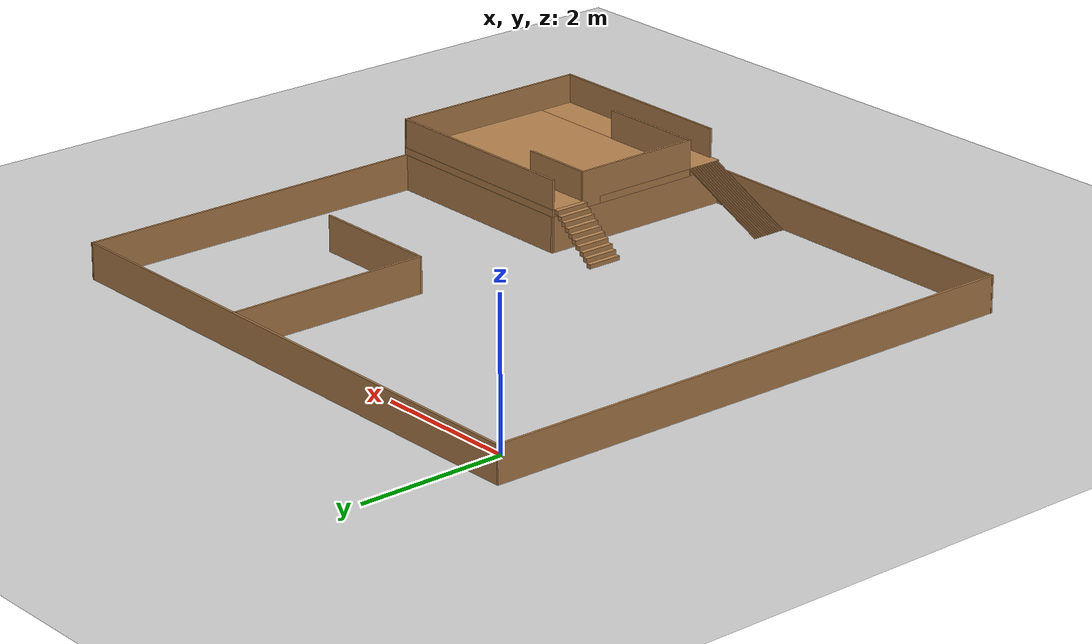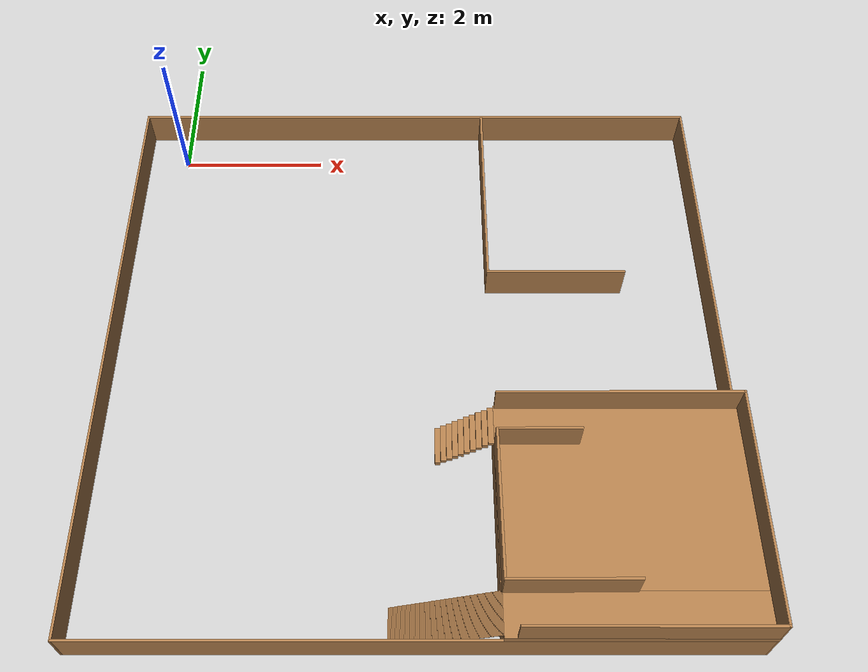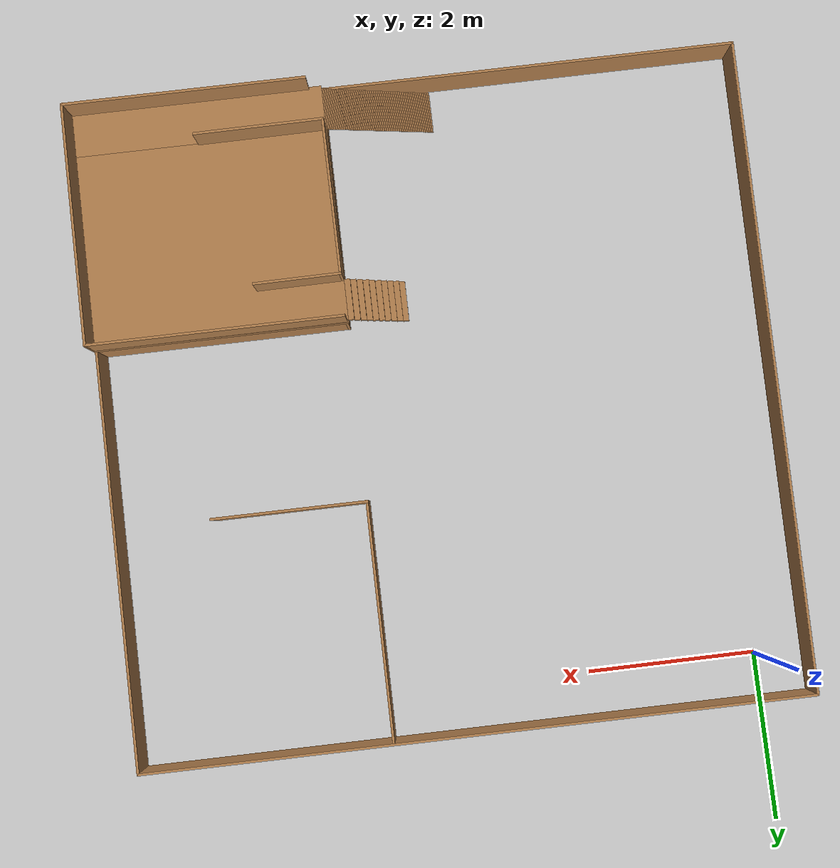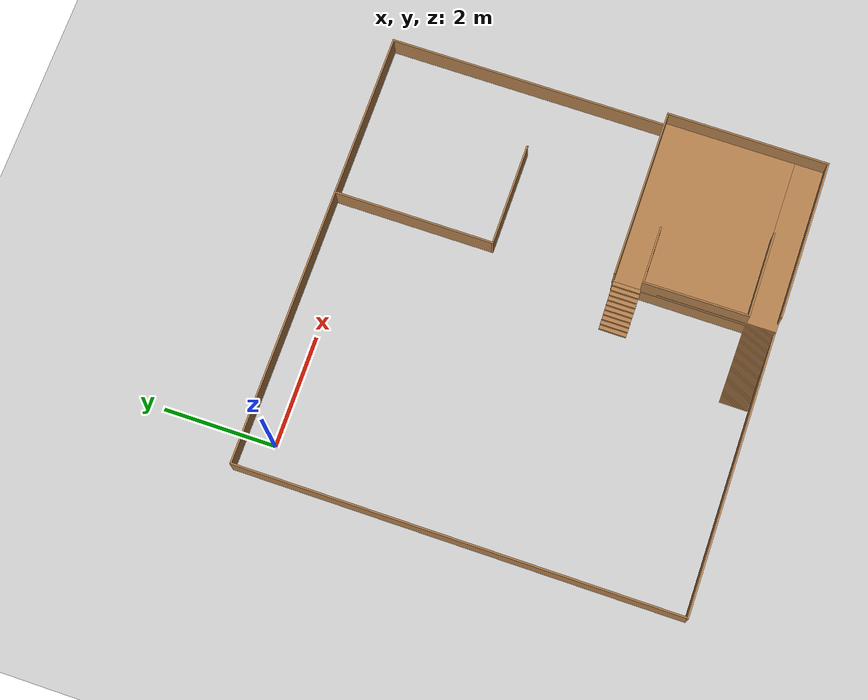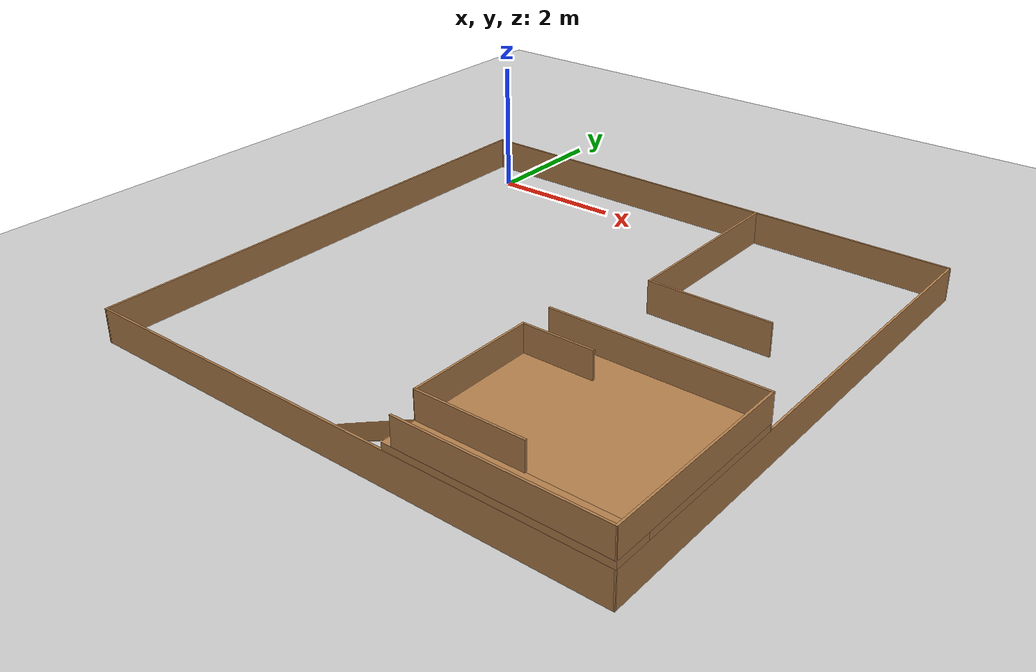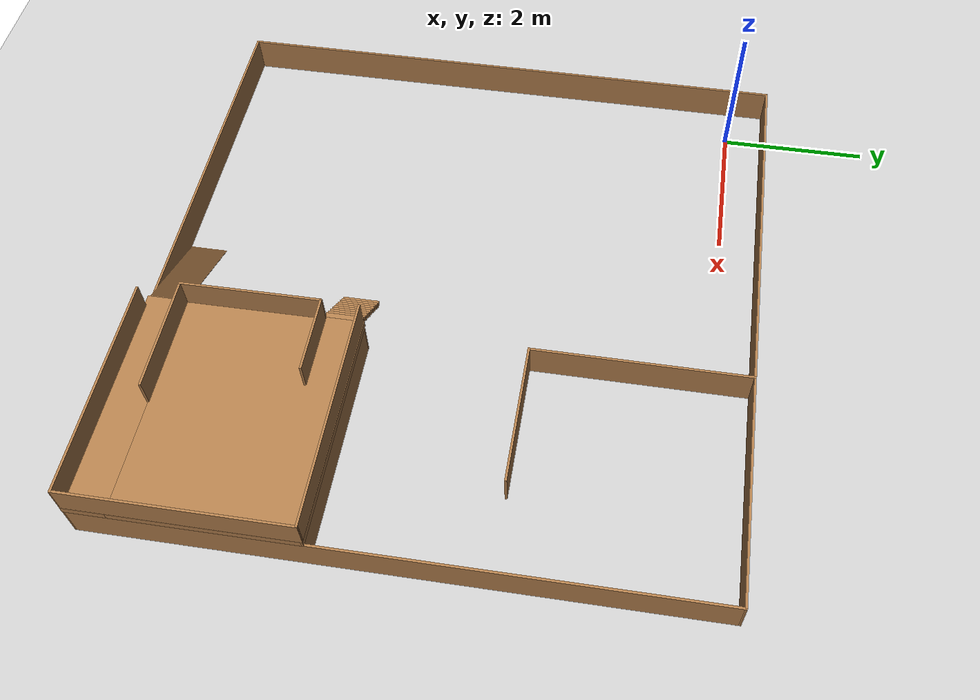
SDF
<sdf version="1.7">
 <world name="default">
  <light name="sun" type="directional">
   <pose>0 0 10 0 -0 0</pose>
   <diffuse>0.8 0.8 0.8 1</diffuse>
   <specular>0.2 0.2 0.2 1</specular>
   <attenuation>
    <range>1000</range>
    <constant>0.9</constant>
    <linear>0.01</linear>
    <quadratic>0.001</quadratic>
   </attenuation>
   <direction>-0.5 0.1 -0.9</direction>
   <spot><inner_angle>0</inner_angle><outer_angle>0</outer_angle><falloff>0</falloff></spot>
  </light>
  <model name="ground_plane">
   <static>1</static>
   <link name="link">
    <collision name="collision">
     <geometry><plane><normal>0 0 1</normal><size>100 100</size></plane></geometry>
     <surface>
      <contact><collide_bitmask>65535</collide_bitmask></contact>
      <friction><ode><mu>100</mu><mu2>50</mu2></ode></friction>
     </surface>
    </collision>
    <visual name="visual">
     <cast_shadows>0</cast_shadows>
     <geometry><plane><normal>0 0 1</normal><size>100 100</size></plane></geometry>
     <material>
      <script><uri>file://media/materials/scripts/gazebo.material</uri><name>Gazebo/Grey</name></script>
     </material>
    </visual>
   </link>
  </model>
  <gravity>0 0 -9.8</gravity>
  <magnetic_field>6e-06 2.3e-05 -4.2e-05</magnetic_field>
  <atmosphere type="adiabatic"/>
  <physics type="ode">
   <max_step_size>0.001</max_step_size>
   <real_time_factor>1</real_time_factor>
   <real_time_update_rate>1000</real_time_update_rate>
  </physics>
  <scene><ambient>0.4 0.4 0.4 1</ambient><background>0.7 0.7 0.7 1</background><shadows>1</shadows></scene>
  <audio><device>default</device></audio>
  <spherical_coordinates>
   <surface_model>EARTH_WGS84</surface_model>
   <latitude_deg>0</latitude_deg>
   <longitude_deg>0</longitude_deg>
   <elevation>0</elevation>
   <heading_deg>0</heading_deg>
  </spherical_coordinates>
  <model name="arena">
   <pose>3.40282 -3.41988 0 0 0 -1.57675</pose>
   <link name="Floor_6">
    <pose>2.49692 2.49323 0.5 0 -0 0</pose>
    <visual name="Floor_6_Visual_0">
     <pose>-1.42421 0 0.05 0 -0 0</pose>
     <geometry><box><size>0.02684 3.05003 0.1</size></box></geometry>
     <material>
      <script><uri>file://media/materials/scripts/gazebo.material</uri><name>Gazebo/Wood</name></script>
      <ambient>1 1 1 1</ambient>
     </material>
     <meta><layer>1</layer></meta>
    </visual>
    <collision name="Floor_6_Collision_0">
     <geometry><box><size>0.02684 3.05003 0.1</size></box></geometry>
     <pose>-1.42421 0 0.05 0 -0 0</pose>
    </collision>
    <visual name="Floor_6_Visual_1">
     <pose>-0.254024 0.000799 0.05 0 -0 0</pose>
     <geometry><box><size>2.31354 3.04843 0.1</size></box></geometry>
     <material>
      <script><uri>file://media/materials/scripts/gazebo.material</uri><name>Gazebo/Wood</name></script>
      <ambient>1 1 1 1</ambient>
     </material>
     <meta><layer>1</layer></meta>
    </visual>
    <collision name="Floor_6_Collision_1">
     <geometry><box><size>2.31354 3.04843 0.1</size></box></geometry>
     <pose>-0.254024 0.000799 0.05 0 -0 0</pose>
    </collision>
    <visual name="Floor_6_Visual_2">
     <pose>1.17019 0.008605 0.05 0 -0 0</pose>
     <geometry><box><size>0.534887 3.03282 0.1</size></box></geometry>
     <material>
      <script><uri>file://media/materials/scripts/gazebo.material</uri><name>Gazebo/Wood</name></script>
      <ambient>1 1 1 1</ambient>
     </material>
     <meta><layer>1</layer></meta>
    </visual>
    <collision name="Floor_6_Collision_2">
     <geometry><box><size>0.534887 3.03282 0.1</size></box></geometry>
     <pose>1.17019 0.008605 0.05 0 -0 0</pose>
    </collision>
   </link>
   <link name="Stairs_11">
    <visual name="Stairs_11_Visual_0">
     <pose>3.65016 -0.298124 0.003 0 0 -3.14159</pose>
     <geometry><box><size>0.501 0.0129 0.006</size></box></geometry>
     <material>
      <script><uri>file://media/materials/scripts/gazebo.material</uri><name>Gazebo/Wood</name></script>
      <ambient>1 1 1 1</ambient>
     </material>
     <meta><layer>0</layer></meta>
    </visual>
    <collision name="Stairs_11_Collision_0">
     <geometry><box><size>0.501 0.0129 0.006</size></box></geometry>
     <pose>3.65016 -0.298124 0.003 0 0 -3.14159</pose>
    </collision>
    <visual name="Stairs_11_Visual_1">
     <pose>3.65016 -0.285224 0.009 0 0 -3.14159</pose>
     <geometry><box><size>0.501 0.0129 0.006</size></box></geometry>
     <material>
      <script><uri>file://media/materials/scripts/gazebo.material</uri><name>Gazebo/Wood</name></script>
      <ambient>1 1 1 1</ambient>
     </material>
     <meta><layer>0</layer></meta>
    </visual>
    <collision name="Stairs_11_Collision_1">
     <geometry><box><size>0.501 0.0129 0.006</size></box></geometry>
     <pose>3.65016 -0.285224 0.009 0 0 -3.14159</pose>
    </collision>
    <visual name="Stairs_11_Visual_2">
     <pose>3.65016 -0.272324 0.015 0 0 -3.14159</pose>
     <geometry><box><size>0.501 0.0129 0.006</size></box></geometry>
     <material>
      <script><uri>file://media/materials/scripts/gazebo.material</uri><name>Gazebo/Wood</name></script>
      <ambient>1 1 1 1</ambient>
     </material>
     <meta><layer>0</layer></meta>
    </visual>
    <collision name="Stairs_11_Collision_2">
     <geometry><box><size>0.501 0.0129 0.006</size></box></geometry>
     <pose>3.65016 -0.272324 0.015 0 0 -3.14159</pose>
    </collision>
    <visual name="Stairs_11_Visual_3">
     <pose>3.65016 -0.259424 0.021 0 0 -3.14159</pose>
     <geometry><box><size>0.501 0.0129 0.006</size></box></geometry>
     <material>
      <script><uri>file://media/materials/scripts/gazebo.material</uri><name>Gazebo/Wood</name></script>
      <ambient>1 1 1 1</ambient>
     </material>
     <meta><layer>0</layer></meta>
    </visual>
    <collision name="Stairs_11_Collision_3">
     <geometry><box><size>0.501 0.0129 0.006</size></box></geometry>
     <pose>3.65016 -0.259424 0.021 0 0 -3.14159</pose>
    </collision>
    <visual name="Stairs_11_Visual_4">
     <pose>3.65016 -0.246524 0.027 0 0 -3.14159</pose>
     <geometry><box><size>0.501 0.0129 0.006</size></box></geometry>
     <material>
      <script><uri>file://media/materials/scripts/gazebo.material</uri><name>Gazebo/Wood</name></script>
      <ambient>1 1 1 1</ambient>
     </material>
     <meta><layer>0</layer></meta>
    </visual>
    <collision name="Stairs_11_Collision_4">
     <geometry><box><size>0.501 0.0129 0.006</size></box></geometry>
     <pose>3.65016 -0.246524 0.027 0 0 -3.14159</pose>
    </collision>
    <visual name="Stairs_11_Visual_5">
     <pose>3.65016 -0.233624 0.033 0 0 -3.14159</pose>
     <geometry><box><size>0.501 0.0129 0.006</size></box></geometry>
     <material>
      <script><uri>file://media/materials/scripts/gazebo.material</uri><name>Gazebo/Wood</name></script>
      <ambient>1 1 1 1</ambient>
     </material>
     <meta><layer>0</layer></meta>
    </visual>
    <collision name="Stairs_11_Collision_5">
     <geometry><box><size>0.501 0.0129 0.006</size></box></geometry>
     <pose>3.65016 -0.233624 0.033 0 0 -3.14159</pose>
    </collision>
    <visual name="Stairs_11_Visual_6">
     <pose>3.65016 -0.220724 0.039 0 0 -3.14159</pose>
     <geometry><box><size>0.501 0.0129 0.006</size></box></geometry>
     <material>
      <script><uri>file://media/materials/scripts/gazebo.material</uri><name>Gazebo/Wood</name></script>
      <ambient>1 1 1 1</ambient>
     </material>
     <meta><layer>0</layer></meta>
    </visual>
    <collision name="Stairs_11_Collision_6">
     <geometry><box><size>0.501 0.0129 0.006</size></box></geometry>
     <pose>3.65016 -0.220724 0.039 0 0 -3.14159</pose>
    </collision>
    <visual name="Stairs_11_Visual_7">
     <pose>3.65016 -0.207824 0.045 0 0 -3.14159</pose>
     <geometry><box><size>0.501 0.0129 0.006</size></box></geometry>
     <material>
      <script><uri>file://media/materials/scripts/gazebo.material</uri><name>Gazebo/Wood</name></script>
      <ambient>1 1 1 1</ambient>
     </material>
     <meta><layer>0</layer></meta>
    </visual>
    <collision name="Stairs_11_Collision_7">
     <geometry><box><size>0.501 0.0129 0.006</size></box></geometry>
     <pose>3.65016 -0.207824 0.045 0 0 -3.14159</pose>
    </collision>
    <visual name="Stairs_11_Visual_8">
     <pose>3.65016 -0.194924 0.051 0 0 -3.14159</pose>
     <geometry><box><size>0.501 0.0129 0.006</size></box></geometry>
     <material>
      <script><uri>file://media/materials/scripts/gazebo.material</uri><name>Gazebo/Wood</name></script>
      <ambient>1 1 1 1</ambient>
     </material>
     <meta><layer>0</layer></meta>
    </visual>
    <collision name="Stairs_11_Collision_8">
     <geometry><box><size>0.501 0.0129 0.006</size></box></geometry>
     <pose>3.65016 -0.194924 0.051 0 0 -3.14159</pose>
    </collision>
    <visual name="Stairs_11_Visual_9">
     <pose>3.65016 -0.182024 0.057 0 0 -3.14159</pose>
     <geometry><box><size>0.501 0.0129 0.006</size></box></geometry>
     <material>
      <script><uri>file://media/materials/scripts/gazebo.material</uri><name>Gazebo/Wood</name></script>
      <ambient>1 1 1 1</ambient>
     </material>
     <meta><layer>0</layer></meta>
    </visual>
    <collision name="Stairs_11_Collision_9">
     <geometry><box><size>0.501 0.0129 0.006</size></box></geometry>
     <pose>3.65016 -0.182024 0.057 0 0 -3.14159</pose>
    </collision>
    <visual name="Stairs_11_Visual_10">
     <pose>3.65016 -0.169124 0.063 0 0 -3.14159</pose>
     <geometry><box><size>0.501 0.0129 0.006</size></box></geometry>
     <material>
      <script><uri>file://media/materials/scripts/gazebo.material</uri><name>Gazebo/Wood</name></script>
      <ambient>1 1 1 1</ambient>
     </material>
     <meta><layer>0</layer></meta>
    </visual>
    <collision name="Stairs_11_Collision_10">
     <geometry><box><size>0.501 0.0129 0.006</size></box></geometry>
     <pose>3.65016 -0.169124 0.063 0 0 -3.14159</pose>
    </collision>
    <visual name="Stairs_11_Visual_11">
     <pose>3.65016 -0.156224 0.069 0 0 -3.14159</pose>
     <geometry><box><size>0.501 0.0129 0.006</size></box></geometry>
     <material>
      <script><uri>file://media/materials/scripts/gazebo.material</uri><name>Gazebo/Wood</name></script>
      <ambient>1 1 1 1</ambient>
     </material>
     <meta><layer>0</layer></meta>
    </visual>
    <collision name="Stairs_11_Collision_11">
     <geometry><box><size>0.501 0.0129 0.006</size></box></geometry>
     <pose>3.65016 -0.156224 0.069 0 0 -3.14159</pose>
    </collision>
    <visual name="Stairs_11_Visual_12">
     <pose>3.65016 -0.143324 0.075 0 0 -3.14159</pose>
     <geometry><box><size>0.501 0.0129 0.006</size></box></geometry>
     <material>
      <script><uri>file://media/materials/scripts/gazebo.material</uri><name>Gazebo/Wood</name></script>
      <ambient>1 1 1 1</ambient>
     </material>
     <meta><layer>0</layer></meta>
    </visual>
    <collision name="Stairs_11_Collision_12">
     <geometry><box><size>0.501 0.0129 0.006</size></box></geometry>
     <pose>3.65016 -0.143324 0.075 0 0 -3.14159</pose>
    </collision>
    <visual name="Stairs_11_Visual_13">
     <pose>3.65016 -0.130424 0.081 0 0 -3.14159</pose>
     <geometry><box><size>0.501 0.0129 0.006</size></box></geometry>
     <material>
      <script><uri>file://media/materials/scripts/gazebo.material</uri><name>Gazebo/Wood</name></script>
      <ambient>1 1 1 1</ambient>
     </material>
     <meta><layer>0</layer></meta>
    </visual>
    <collision name="Stairs_11_Collision_13">
     <geometry><box><size>0.501 0.0129 0.006</size></box></geometry>
     <pose>3.65016 -0.130424 0.081 0 0 -3.14159</pose>
    </collision>
    <visual name="Stairs_11_Visual_14">
     <pose>3.65016 -0.117524 0.087 0 0 -3.14159</pose>
     <geometry><box><size>0.501 0.0129 0.006</size></box></geometry>
     <material>
      <script><uri>file://media/materials/scripts/gazebo.material</uri><name>Gazebo/Wood</name></script>
      <ambient>1 1 1 1</ambient>
     </material>
     <meta><layer>0</layer></meta>
    </visual>
    <collision name="Stairs_11_Collision_14">
     <geometry><box><size>0.501 0.0129 0.006</size></box></geometry>
     <pose>3.65016 -0.117524 0.087 0 0 -3.14159</pose>
    </collision>
    <visual name="Stairs_11_Visual_15">
     <pose>3.65016 -0.104624 0.093 0 0 -3.14159</pose>
     <geometry><box><size>0.501 0.0129 0.006</size></box></geometry>
     <material>
      <script><uri>file://media/materials/scripts/gazebo.material</uri><name>Gazebo/Wood</name></script>
      <ambient>1 1 1 1</ambient>
     </material>
     <meta><layer>0</layer></meta>
    </visual>
    <collision name="Stairs_11_Collision_15">
     <geometry><box><size>0.501 0.0129 0.006</size></box></geometry>
     <pose>3.65016 -0.104624 0.093 0 0 -3.14159</pose>
    </collision>
    <visual name="Stairs_11_Visual_16">
     <pose>3.65016 -0.091724 0.099 0 0 -3.14159</pose>
     <geometry><box><size>0.501 0.0129 0.006</size></box></geometry>
     <material>
      <script><uri>file://media/materials/scripts/gazebo.material</uri><name>Gazebo/Wood</name></script>
      <ambient>1 1 1 1</ambient>
     </material>
     <meta><layer>0</layer></meta>
    </visual>
    <collision name="Stairs_11_Collision_16">
     <geometry><box><size>0.501 0.0129 0.006</size></box></geometry>
     <pose>3.65016 -0.091724 0.099 0 0 -3.14159</pose>
    </collision>
    <visual name="Stairs_11_Visual_17">
     <pose>3.65016 -0.078824 0.105 0 0 -3.14159</pose>
     <geometry><box><size>0.501 0.0129 0.006</size></box></geometry>
     <material>
      <script><uri>file://media/materials/scripts/gazebo.material</uri><name>Gazebo/Wood</name></script>
      <ambient>1 1 1 1</ambient>
     </material>
     <meta><layer>0</layer></meta>
    </visual>
    <collision name="Stairs_11_Collision_17">
     <geometry><box><size>0.501 0.0129 0.006</size></box></geometry>
     <pose>3.65016 -0.078824 0.105 0 0 -3.14159</pose>
    </collision>
    <visual name="Stairs_11_Visual_18">
     <pose>3.65016 -0.065924 0.111 0 0 -3.14159</pose>
     <geometry><box><size>0.501 0.0129 0.006</size></box></geometry>
     <material>
      <script><uri>file://media/materials/scripts/gazebo.material</uri><name>Gazebo/Wood</name></script>
      <ambient>1 1 1 1</ambient>
     </material>
     <meta><layer>0</layer></meta>
    </visual>
    <collision name="Stairs_11_Collision_18">
     <geometry><box><size>0.501 0.0129 0.006</size></box></geometry>
     <pose>3.65016 -0.065924 0.111 0 0 -3.14159</pose>
    </collision>
    <visual name="Stairs_11_Visual_19">
     <pose>3.65016 -0.053024 0.117 0 0 -3.14159</pose>
     <geometry><box><size>0.501 0.0129 0.006</size></box></geometry>
     <material>
      <script><uri>file://media/materials/scripts/gazebo.material</uri><name>Gazebo/Wood</name></script>
      <ambient>1 1 1 1</ambient>
     </material>
     <meta><layer>0</layer></meta>
    </visual>
    <collision name="Stairs_11_Collision_19">
     <geometry><box><size>0.501 0.0129 0.006</size></box></geometry>
     <pose>3.65016 -0.053024 0.117 0 0 -3.14159</pose>
    </collision>
    <visual name="Stairs_11_Visual_20">
     <pose>3.65016 -0.040124 0.123 0 0 -3.14159</pose>
     <geometry><box><size>0.501 0.0129 0.006</size></box></geometry>
     <material>
      <script><uri>file://media/materials/scripts/gazebo.material</uri><name>Gazebo/Wood</name></script>
      <ambient>1 1 1 1</ambient>
     </material>
     <meta><layer>0</layer></meta>
    </visual>
    <collision name="Stairs_11_Collision_20">
     <geometry><box><size>0.501 0.0129 0.006</size></box></geometry>
     <pose>3.65016 -0.040124 0.123 0 0 -3.14159</pose>
    </collision>
    <visual name="Stairs_11_Visual_21">
     <pose>3.65016 -0.027224 0.129 0 0 -3.14159</pose>
     <geometry><box><size>0.501 0.0129 0.006</size></box></geometry>
     <material>
      <script><uri>file://media/materials/scripts/gazebo.material</uri><name>Gazebo/Wood</name></script>
      <ambient>1 1 1 1</ambient>
     </material>
     <meta><layer>0</layer></meta>
    </visual>
    <collision name="Stairs_11_Collision_21">
     <geometry><box><size>0.501 0.0129 0.006</size></box></geometry>
     <pose>3.65016 -0.027224 0.129 0 0 -3.14159</pose>
    </collision>
    <visual name="Stairs_11_Visual_22">
     <pose>3.65016 -0.014324 0.135 0 0 -3.14159</pose>
     <geometry><box><size>0.501 0.0129 0.006</size></box></geometry>
     <material>
      <script><uri>file://media/materials/scripts/gazebo.material</uri><name>Gazebo/Wood</name></script>
      <ambient>1 1 1 1</ambient>
     </material>
     <meta><layer>0</layer></meta>
    </visual>
    <collision name="Stairs_11_Collision_22">
     <geometry><box><size>0.501 0.0129 0.006</size></box></geometry>
     <pose>3.65016 -0.014324 0.135 0 0 -3.14159</pose>
    </collision>
    <visual name="Stairs_11_Visual_23">
     <pose>3.65016 -0.001424 0.141 0 0 -3.14159</pose>
     <geometry><box><size>0.501 0.0129 0.006</size></box></geometry>
     <material>
      <script><uri>file://media/materials/scripts/gazebo.material</uri><name>Gazebo/Wood</name></script>
      <ambient>1 1 1 1</ambient>
     </material>
     <meta><layer>0</layer></meta>
    </visual>
    <collision name="Stairs_11_Collision_23">
     <geometry><box><size>0.501 0.0129 0.006</size></box></geometry>
     <pose>3.65016 -0.001424 0.141 0 0 -3.14159</pose>
    </collision>
    <visual name="Stairs_11_Visual_24">
     <pose>3.65016 0.011476 0.147 0 0 -3.14159</pose>
     <geometry><box><size>0.501 0.0129 0.006</size></box></geometry>
     <material>
      <script><uri>file://media/materials/scripts/gazebo.material</uri><name>Gazebo/Wood</name></script>
      <ambient>1 1 1 1</ambient>
     </material>
     <meta><layer>0</layer></meta>
    </visual>
    <collision name="Stairs_11_Collision_24">
     <geometry><box><size>0.501 0.0129 0.006</size></box></geometry>
     <pose>3.65016 0.011476 0.147 0 0 -3.14159</pose>
    </collision>
    <visual name="Stairs_11_Visual_25">
     <pose>3.65016 0.024376 0.153 0 0 -3.14159</pose>
     <geometry><box><size>0.501 0.0129 0.006</size></box></geometry>
     <material>
      <script><uri>file://media/materials/scripts/gazebo.material</uri><name>Gazebo/Wood</name></script>
      <ambient>1 1 1 1</ambient>
     </material>
     <meta><layer>0</layer></meta>
    </visual>
    <collision name="Stairs_11_Collision_25">
     <geometry><box><size>0.501 0.0129 0.006</size></box></geometry>
     <pose>3.65016 0.024376 0.153 0 0 -3.14159</pose>
    </collision>
    <visual name="Stairs_11_Visual_26">
     <pose>3.65016 0.037276 0.159 0 0 -3.14159</pose>
     <geometry><box><size>0.501 0.0129 0.006</size></box></geometry>
     <material>
      <script><uri>file://media/materials/scripts/gazebo.material</uri><name>Gazebo/Wood</name></script>
      <ambient>1 1 1 1</ambient>
     </material>
     <meta><layer>0</layer></meta>
    </visual>
    <collision name="Stairs_11_Collision_26">
     <geometry><box><size>0.501 0.0129 0.006</size></box></geometry>
     <pose>3.65016 0.037276 0.159 0 0 -3.14159</pose>
    </collision>
    <visual name="Stairs_11_Visual_27">
     <pose>3.65016 0.050176 0.165 0 0 -3.14159</pose>
     <geometry><box><size>0.501 0.0129 0.006</size></box></geometry>
     <material>
      <script><uri>file://media/materials/scripts/gazebo.material</uri><name>Gazebo/Wood</name></script>
      <ambient>1 1 1 1</ambient>
     </material>
     <meta><layer>0</layer></meta>
    </visual>
    <collision name="Stairs_11_Collision_27">
     <geometry><box><size>0.501 0.0129 0.006</size></box></geometry>
     <pose>3.65016 0.050176 0.165 0 0 -3.14159</pose>
    </collision>
    <visual name="Stairs_11_Visual_28">
     <pose>3.65016 0.063076 0.171 0 0 -3.14159</pose>
     <geometry><box><size>0.501 0.0129 0.006</size></box></geometry>
     <material>
      <script><uri>file://media/materials/scripts/gazebo.material</uri><name>Gazebo/Wood</name></script>
      <ambient>1 1 1 1</ambient>
     </material>
     <meta><layer>0</layer></meta>
    </visual>
    <collision name="Stairs_11_Collision_28">
     <geometry><box><size>0.501 0.0129 0.006</size></box></geometry>
     <pose>3.65016 0.063076 0.171 0 0 -3.14159</pose>
    </collision>
    <visual name="Stairs_11_Visual_29">
     <pose>3.65016 0.075976 0.177 0 0 -3.14159</pose>
     <geometry><box><size>0.501 0.0129 0.006</size></box></geometry>
     <material>
      <script><uri>file://media/materials/scripts/gazebo.material</uri><name>Gazebo/Wood</name></script>
      <ambient>1 1 1 1</ambient>
     </material>
     <meta><layer>0</layer></meta>
    </visual>
    <collision name="Stairs_11_Collision_29">
     <geometry><box><size>0.501 0.0129 0.006</size></box></geometry>
     <pose>3.65016 0.075976 0.177 0 0 -3.14159</pose>
    </collision>
    <visual name="Stairs_11_Visual_30">
     <pose>3.65016 0.088876 0.183 0 0 -3.14159</pose>
     <geometry><box><size>0.501 0.0129 0.006</size></box></geometry>
     <material>
      <script><uri>file://media/materials/scripts/gazebo.material</uri><name>Gazebo/Wood</name></script>
      <ambient>1 1 1 1</ambient>
     </material>
     <meta><layer>0</layer></meta>
    </visual>
    <collision name="Stairs_11_Collision_30">
     <geometry><box><size>0.501 0.0129 0.006</size></box></geometry>
     <pose>3.65016 0.088876 0.183 0 0 -3.14159</pose>
    </collision>
    <visual name="Stairs_11_Visual_31">
     <pose>3.65016 0.101776 0.189 0 0 -3.14159</pose>
     <geometry><box><size>0.501 0.0129 0.006</size></box></geometry>
     <material>
      <script><uri>file://media/materials/scripts/gazebo.material</uri><name>Gazebo/Wood</name></script>
      <ambient>1 1 1 1</ambient>
     </material>
     <meta><layer>0</layer></meta>
    </visual>
    <collision name="Stairs_11_Collision_31">
     <geometry><box><size>0.501 0.0129 0.006</size></box></geometry>
     <pose>3.65016 0.101776 0.189 0 0 -3.14159</pose>
    </collision>
    <visual name="Stairs_11_Visual_32">
     <pose>3.65016 0.114676 0.195 0 0 -3.14159</pose>
     <geometry><box><size>0.501 0.0129 0.006</size></box></geometry>
     <material>
      <script><uri>file://media/materials/scripts/gazebo.material</uri><name>Gazebo/Wood</name></script>
      <ambient>1 1 1 1</ambient>
     </material>
     <meta><layer>0</layer></meta>
    </visual>
    <collision name="Stairs_11_Collision_32">
     <geometry><box><size>0.501 0.0129 0.006</size></box></geometry>
     <pose>3.65016 0.114676 0.195 0 0 -3.14159</pose>
    </collision>
    <visual name="Stairs_11_Visual_33">
     <pose>3.65016 0.127576 0.201 0 0 -3.14159</pose>
     <geometry><box><size>0.501 0.0129 0.006</size></box></geometry>
     <material>
      <script><uri>file://media/materials/scripts/gazebo.material</uri><name>Gazebo/Wood</name></script>
      <ambient>1 1 1 1</ambient>
     </material>
     <meta><layer>0</layer></meta>
    </visual>
    <collision name="Stairs_11_Collision_33">
     <geometry><box><size>0.501 0.0129 0.006</size></box></geometry>
     <pose>3.65016 0.127576 0.201 0 0 -3.14159</pose>
    </collision>
    <visual name="Stairs_11_Visual_34">
     <pose>3.65016 0.140476 0.207 0 0 -3.14159</pose>
     <geometry><box><size>0.501 0.0129 0.006</size></box></geometry>
     <material>
      <script><uri>file://media/materials/scripts/gazebo.material</uri><name>Gazebo/Wood</name></script>
      <ambient>1 1 1 1</ambient>
     </material>
     <meta><layer>0</layer></meta>
    </visual>
    <collision name="Stairs_11_Collision_34">
     <geometry><box><size>0.501 0.0129 0.006</size></box></geometry>
     <pose>3.65016 0.140476 0.207 0 0 -3.14159</pose>
    </collision>
    <visual name="Stairs_11_Visual_35">
     <pose>3.65016 0.153376 0.213 0 0 -3.14159</pose>
     <geometry><box><size>0.501 0.0129 0.006</size></box></geometry>
     <material>
      <script><uri>file://media/materials/scripts/gazebo.material</uri><name>Gazebo/Wood</name></script>
      <ambient>1 1 1 1</ambient>
     </material>
     <meta><layer>0</layer></meta>
    </visual>
    <collision name="Stairs_11_Collision_35">
     <geometry><box><size>0.501 0.0129 0.006</size></box></geometry>
     <pose>3.65016 0.153376 0.213 0 0 -3.14159</pose>
    </collision>
    <visual name="Stairs_11_Visual_36">
     <pose>3.65016 0.166276 0.219 0 0 -3.14159</pose>
     <geometry><box><size>0.501 0.0129 0.006</size></box></geometry>
     <material>
      <script><uri>file://media/materials/scripts/gazebo.material</uri><name>Gazebo/Wood</name></script>
      <ambient>1 1 1 1</ambient>
     </material>
     <meta><layer>0</layer></meta>
    </visual>
    <collision name="Stairs_11_Collision_36">
     <geometry><box><size>0.501 0.0129 0.006</size></box></geometry>
     <pose>3.65016 0.166276 0.219 0 0 -3.14159</pose>
    </collision>
    <visual name="Stairs_11_Visual_37">
     <pose>3.65016 0.179176 0.225 0 0 -3.14159</pose>
     <geometry><box><size>0.501 0.0129 0.006</size></box></geometry>
     <material>
      <script><uri>file://media/materials/scripts/gazebo.material</uri><name>Gazebo/Wood</name></script>
      <ambient>1 1 1 1</ambient>
     </material>
     <meta><layer>0</layer></meta>
    </visual>
    <collision name="Stairs_11_Collision_37">
     <geometry><box><size>0.501 0.0129 0.006</size></box></geometry>
     <pose>3.65016 0.179176 0.225 0 0 -3.14159</pose>
    </collision>
    <visual name="Stairs_11_Visual_38">
     <pose>3.65016 0.192076 0.231 0 0 -3.14159</pose>
     <geometry><box><size>0.501 0.0129 0.006</size></box></geometry>
     <material>
      <script><uri>file://media/materials/scripts/gazebo.material</uri><name>Gazebo/Wood</name></script>
      <ambient>1 1 1 1</ambient>
     </material>
     <meta><layer>0</layer></meta>
    </visual>
    <collision name="Stairs_11_Collision_38">
     <geometry><box><size>0.501 0.0129 0.006</size></box></geometry>
     <pose>3.65016 0.192076 0.231 0 0 -3.14159</pose>
    </collision>
    <visual name="Stairs_11_Visual_39">
     <pose>3.65016 0.204976 0.237 0 0 -3.14159</pose>
     <geometry><box><size>0.501 0.0129 0.006</size></box></geometry>
     <material>
      <script><uri>file://media/materials/scripts/gazebo.material</uri><name>Gazebo/Wood</name></script>
      <ambient>1 1 1 1</ambient>
     </material>
     <meta><layer>0</layer></meta>
    </visual>
    <collision name="Stairs_11_Collision_39">
     <geometry><box><size>0.501 0.0129 0.006</size></box></geometry>
     <pose>3.65016 0.204976 0.237 0 0 -3.14159</pose>
    </collision>
    <visual name="Stairs_11_Visual_40">
     <pose>3.65016 0.217876 0.243 0 0 -3.14159</pose>
     <geometry><box><size>0.501 0.0129 0.006</size></box></geometry>
     <material>
      <script><uri>file://media/materials/scripts/gazebo.material</uri><name>Gazebo/Wood</name></script>
      <ambient>1 1 1 1</ambient>
     </material>
     <meta><layer>0</layer></meta>
    </visual>
    <collision name="Stairs_11_Collision_40">
     <geometry><box><size>0.501 0.0129 0.006</size></box></geometry>
     <pose>3.65016 0.217876 0.243 0 0 -3.14159</pose>
    </collision>
    <visual name="Stairs_11_Visual_41">
     <pose>3.65016 0.230776 0.249 0 0 -3.14159</pose>
     <geometry><box><size>0.501 0.0129 0.006</size></box></geometry>
     <material>
      <script><uri>file://media/materials/scripts/gazebo.material</uri><name>Gazebo/Wood</name></script>
      <ambient>1 1 1 1</ambient>
     </material>
     <meta><layer>0</layer></meta>
    </visual>
    <collision name="Stairs_11_Collision_41">
     <geometry><box><size>0.501 0.0129 0.006</size></box></geometry>
     <pose>3.65016 0.230776 0.249 0 0 -3.14159</pose>
    </collision>
    <visual name="Stairs_11_Visual_42">
     <pose>3.65016 0.243676 0.255 0 0 -3.14159</pose>
     <geometry><box><size>0.501 0.0129 0.006</size></box></geometry>
     <material>
      <script><uri>file://media/materials/scripts/gazebo.material</uri><name>Gazebo/Wood</name></script>
      <ambient>1 1 1 1</ambient>
     </material>
     <meta><layer>0</layer></meta>
    </visual>
    <collision name="Stairs_11_Collision_42">
     <geometry><box><size>0.501 0.0129 0.006</size></box></geometry>
     <pose>3.65016 0.243676 0.255 0 0 -3.14159</pose>
    </collision>
    <visual name="Stairs_11_Visual_43">
     <pose>3.65016 0.256576 0.261 0 0 -3.14159</pose>
     <geometry><box><size>0.501 0.0129 0.006</size></box></geometry>
     <material>
      <script><uri>file://media/materials/scripts/gazebo.material</uri><name>Gazebo/Wood</name></script>
      <ambient>1 1 1 1</ambient>
     </material>
     <meta><layer>0</layer></meta>
    </visual>
    <collision name="Stairs_11_Collision_43">
     <geometry><box><size>0.501 0.0129 0.006</size></box></geometry>
     <pose>3.65016 0.256576 0.261 0 0 -3.14159</pose>
    </collision>
    <visual name="Stairs_11_Visual_44">
     <pose>3.65016 0.269476 0.267 0 0 -3.14159</pose>
     <geometry><box><size>0.501 0.0129 0.006</size></box></geometry>
     <material>
      <script><uri>file://media/materials/scripts/gazebo.material</uri><name>Gazebo/Wood</name></script>
      <ambient>1 1 1 1</ambient>
     </material>
     <meta><layer>0</layer></meta>
    </visual>
    <collision name="Stairs_11_Collision_44">
     <geometry><box><size>0.501 0.0129 0.006</size></box></geometry>
     <pose>3.65016 0.269476 0.267 0 0 -3.14159</pose>
    </collision>
    <visual name="Stairs_11_Visual_45">
     <pose>3.65016 0.282376 0.273 0 0 -3.14159</pose>
     <geometry><box><size>0.501 0.0129 0.006</size></box></geometry>
     <material>
      <script><uri>file://media/materials/scripts/gazebo.material</uri><name>Gazebo/Wood</name></script>
      <ambient>1 1 1 1</ambient>
     </material>
     <meta><layer>0</layer></meta>
    </visual>
    <collision name="Stairs_11_Collision_45">
     <geometry><box><size>0.501 0.0129 0.006</size></box></geometry>
     <pose>3.65016 0.282376 0.273 0 0 -3.14159</pose>
    </collision>
    <visual name="Stairs_11_Visual_46">
     <pose>3.65016 0.295276 0.279 0 0 -3.14159</pose>
     <geometry><box><size>0.501 0.0129 0.006</size></box></geometry>
     <material>
      <script><uri>file://media/materials/scripts/gazebo.material</uri><name>Gazebo/Wood</name></script>
      <ambient>1 1 1 1</ambient>
     </material>
     <meta><layer>0</layer></meta>
    </visual>
    <collision name="Stairs_11_Collision_46">
     <geometry><box><size>0.501 0.0129 0.006</size></box></geometry>
     <pose>3.65016 0.295276 0.279 0 0 -3.14159</pose>
    </collision>
    <visual name="Stairs_11_Visual_47">
     <pose>3.65016 0.308176 0.285 0 0 -3.14159</pose>
     <geometry><box><size>0.501 0.0129 0.006</size></box></geometry>
     <material>
      <script><uri>file://media/materials/scripts/gazebo.material</uri><name>Gazebo/Wood</name></script>
      <ambient>1 1 1 1</ambient>
     </material>
     <meta><layer>0</layer></meta>
    </visual>
    <collision name="Stairs_11_Collision_47">
     <geometry><box><size>0.501 0.0129 0.006</size></box></geometry>
     <pose>3.65016 0.308176 0.285 0 0 -3.14159</pose>
    </collision>
    <visual name="Stairs_11_Visual_48">
     <pose>3.65016 0.321076 0.291 0 0 -3.14159</pose>
     <geometry><box><size>0.501 0.0129 0.006</size></box></geometry>
     <material>
      <script><uri>file://media/materials/scripts/gazebo.material</uri><name>Gazebo/Wood</name></script>
      <ambient>1 1 1 1</ambient>
     </material>
     <meta><layer>0</layer></meta>
    </visual>
    <collision name="Stairs_11_Collision_48">
     <geometry><box><size>0.501 0.0129 0.006</size></box></geometry>
     <pose>3.65016 0.321076 0.291 0 0 -3.14159</pose>
    </collision>
    <visual name="Stairs_11_Visual_49">
     <pose>3.65016 0.333976 0.297 0 0 -3.14159</pose>
     <geometry><box><size>0.501 0.0129 0.006</size></box></geometry>
     <material>
      <script><uri>file://media/materials/scripts/gazebo.material</uri><name>Gazebo/Wood</name></script>
      <ambient>1 1 1 1</ambient>
     </material>
     <meta><layer>0</layer></meta>
    </visual>
    <collision name="Stairs_11_Collision_49">
     <geometry><box><size>0.501 0.0129 0.006</size></box></geometry>
     <pose>3.65016 0.333976 0.297 0 0 -3.14159</pose>
    </collision>
    <visual name="Stairs_11_Visual_50">
     <pose>3.65016 0.346876 0.303 0 0 -3.14159</pose>
     <geometry><box><size>0.501 0.0129 0.006</size></box></geometry>
     <material>
      <script><uri>file://media/materials/scripts/gazebo.material</uri><name>Gazebo/Wood</name></script>
      <ambient>1 1 1 1</ambient>
     </material>
     <meta><layer>0</layer></meta>
    </visual>
    <collision name="Stairs_11_Collision_50">
     <geometry><box><size>0.501 0.0129 0.006</size></box></geometry>
     <pose>3.65016 0.346876 0.303 0 0 -3.14159</pose>
    </collision>
    <visual name="Stairs_11_Visual_51">
     <pose>3.65016 0.359776 0.309 0 0 -3.14159</pose>
     <geometry><box><size>0.501 0.0129 0.006</size></box></geometry>
     <material>
      <script><uri>file://media/materials/scripts/gazebo.material</uri><name>Gazebo/Wood</name></script>
      <ambient>1 1 1 1</ambient>
     </material>
     <meta><layer>0</layer></meta>
    </visual>
    <collision name="Stairs_11_Collision_51">
     <geometry><box><size>0.501 0.0129 0.006</size></box></geometry>
     <pose>3.65016 0.359776 0.309 0 0 -3.14159</pose>
    </collision>
    <visual name="Stairs_11_Visual_52">
     <pose>3.65016 0.372676 0.315 0 0 -3.14159</pose>
     <geometry><box><size>0.501 0.0129 0.006</size></box></geometry>
     <material>
      <script><uri>file://media/materials/scripts/gazebo.material</uri><name>Gazebo/Wood</name></script>
      <ambient>1 1 1 1</ambient>
     </material>
     <meta><layer>0</layer></meta>
    </visual>
    <collision name="Stairs_11_Collision_52">
     <geometry><box><size>0.501 0.0129 0.006</size></box></geometry>
     <pose>3.65016 0.372676 0.315 0 0 -3.14159</pose>
    </collision>
    <visual name="Stairs_11_Visual_53">
     <pose>3.65016 0.385576 0.321 0 0 -3.14159</pose>
     <geometry><box><size>0.501 0.0129 0.006</size></box></geometry>
     <material>
      <script><uri>file://media/materials/scripts/gazebo.material</uri><name>Gazebo/Wood</name></script>
      <ambient>1 1 1 1</ambient>
     </material>
     <meta><layer>0</layer></meta>
    </visual>
    <collision name="Stairs_11_Collision_53">
     <geometry><box><size>0.501 0.0129 0.006</size></box></geometry>
     <pose>3.65016 0.385576 0.321 0 0 -3.14159</pose>
    </collision>
    <visual name="Stairs_11_Visual_54">
     <pose>3.65016 0.398476 0.327 0 0 -3.14159</pose>
     <geometry><box><size>0.501 0.0129 0.006</size></box></geometry>
     <material>
      <script><uri>file://media/materials/scripts/gazebo.material</uri><name>Gazebo/Wood</name></script>
      <ambient>1 1 1 1</ambient>
     </material>
     <meta><layer>0</layer></meta>
    </visual>
    <collision name="Stairs_11_Collision_54">
     <geometry><box><size>0.501 0.0129 0.006</size></box></geometry>
     <pose>3.65016 0.398476 0.327 0 0 -3.14159</pose>
    </collision>
    <visual name="Stairs_11_Visual_55">
     <pose>3.65016 0.411376 0.333 0 0 -3.14159</pose>
     <geometry><box><size>0.501 0.0129 0.006</size></box></geometry>
     <material>
      <script><uri>file://media/materials/scripts/gazebo.material</uri><name>Gazebo/Wood</name></script>
      <ambient>1 1 1 1</ambient>
     </material>
     <meta><layer>0</layer></meta>
    </visual>
    <collision name="Stairs_11_Collision_55">
     <geometry><box><size>0.501 0.0129 0.006</size></box></geometry>
     <pose>3.65016 0.411376 0.333 0 0 -3.14159</pose>
    </collision>
    <visual name="Stairs_11_Visual_56">
     <pose>3.65016 0.424276 0.339 0 0 -3.14159</pose>
     <geometry><box><size>0.501 0.0129 0.006</size></box></geometry>
     <material>
      <script><uri>file://media/materials/scripts/gazebo.material</uri><name>Gazebo/Wood</name></script>
      <ambient>1 1 1 1</ambient>
     </material>
     <meta><layer>0</layer></meta>
    </visual>
    <collision name="Stairs_11_Collision_56">
     <geometry><box><size>0.501 0.0129 0.006</size></box></geometry>
     <pose>3.65016 0.424276 0.339 0 0 -3.14159</pose>
    </collision>
    <visual name="Stairs_11_Visual_57">
     <pose>3.65016 0.437176 0.345 0 0 -3.14159</pose>
     <geometry><box><size>0.501 0.0129 0.006</size></box></geometry>
     <material>
      <script><uri>file://media/materials/scripts/gazebo.material</uri><name>Gazebo/Wood</name></script>
      <ambient>1 1 1 1</ambient>
     </material>
     <meta><layer>0</layer></meta>
    </visual>
    <collision name="Stairs_11_Collision_57">
     <geometry><box><size>0.501 0.0129 0.006</size></box></geometry>
     <pose>3.65016 0.437176 0.345 0 0 -3.14159</pose>
    </collision>
    <visual name="Stairs_11_Visual_58">
     <pose>3.65016 0.450076 0.351 0 0 -3.14159</pose>
     <geometry><box><size>0.501 0.0129 0.006</size></box></geometry>
     <material>
      <script><uri>file://media/materials/scripts/gazebo.material</uri><name>Gazebo/Wood</name></script>
      <ambient>1 1 1 1</ambient>
     </material>
     <meta><layer>0</layer></meta>
    </visual>
    <collision name="Stairs_11_Collision_58">
     <geometry><box><size>0.501 0.0129 0.006</size></box></geometry>
     <pose>3.65016 0.450076 0.351 0 0 -3.14159</pose>
    </collision>
    <visual name="Stairs_11_Visual_59">
     <pose>3.65016 0.462976 0.357 0 0 -3.14159</pose>
     <geometry><box><size>0.501 0.0129 0.006</size></box></geometry>
     <material>
      <script><uri>file://media/materials/scripts/gazebo.material</uri><name>Gazebo/Wood</name></script>
      <ambient>1 1 1 1</ambient>
     </material>
     <meta><layer>0</layer></meta>
    </visual>
    <collision name="Stairs_11_Collision_59">
     <geometry><box><size>0.501 0.0129 0.006</size></box></geometry>
     <pose>3.65016 0.462976 0.357 0 0 -3.14159</pose>
    </collision>
    <visual name="Stairs_11_Visual_60">
     <pose>3.65016 0.475876 0.363 0 0 -3.14159</pose>
     <geometry><box><size>0.501 0.0129 0.006</size></box></geometry>
     <material>
      <script><uri>file://media/materials/scripts/gazebo.material</uri><name>Gazebo/Wood</name></script>
      <ambient>1 1 1 1</ambient>
     </material>
     <meta><layer>0</layer></meta>
    </visual>
    <collision name="Stairs_11_Collision_60">
     <geometry><box><size>0.501 0.0129 0.006</size></box></geometry>
     <pose>3.65016 0.475876 0.363 0 0 -3.14159</pose>
    </collision>
    <visual name="Stairs_11_Visual_61">
     <pose>3.65016 0.488776 0.369 0 0 -3.14159</pose>
     <geometry><box><size>0.501 0.0129 0.006</size></box></geometry>
     <material>
      <script><uri>file://media/materials/scripts/gazebo.material</uri><name>Gazebo/Wood</name></script>
      <ambient>1 1 1 1</ambient>
     </material>
     <meta><layer>0</layer></meta>
    </visual>
    <collision name="Stairs_11_Collision_61">
     <geometry><box><size>0.501 0.0129 0.006</size></box></geometry>
     <pose>3.65016 0.488776 0.369 0 0 -3.14159</pose>
    </collision>
    <visual name="Stairs_11_Visual_62">
     <pose>3.65016 0.501676 0.375 0 0 -3.14159</pose>
     <geometry><box><size>0.501 0.0129 0.006</size></box></geometry>
     <material>
      <script><uri>file://media/materials/scripts/gazebo.material</uri><name>Gazebo/Wood</name></script>
      <ambient>1 1 1 1</ambient>
     </material>
     <meta><layer>0</layer></meta>
    </visual>
    <collision name="Stairs_11_Collision_62">
     <geometry><box><size>0.501 0.0129 0.006</size></box></geometry>
     <pose>3.65016 0.501676 0.375 0 0 -3.14159</pose>
    </collision>
    <visual name="Stairs_11_Visual_63">
     <pose>3.65016 0.514576 0.381 0 0 -3.14159</pose>
     <geometry><box><size>0.501 0.0129 0.006</size></box></geometry>
     <material>
      <script><uri>file://media/materials/scripts/gazebo.material</uri><name>Gazebo/Wood</name></script>
      <ambient>1 1 1 1</ambient>
     </material>
     <meta><layer>0</layer></meta>
    </visual>
    <collision name="Stairs_11_Collision_63">
     <geometry><box><size>0.501 0.0129 0.006</size></box></geometry>
     <pose>3.65016 0.514576 0.381 0 0 -3.14159</pose>
    </collision>
    <visual name="Stairs_11_Visual_64">
     <pose>3.65016 0.527476 0.387 0 0 -3.14159</pose>
     <geometry><box><size>0.501 0.0129 0.006</size></box></geometry>
     <material>
      <script><uri>file://media/materials/scripts/gazebo.material</uri><name>Gazebo/Wood</name></script>
      <ambient>1 1 1 1</ambient>
     </material>
     <meta><layer>0</layer></meta>
    </visual>
    <collision name="Stairs_11_Collision_64">
     <geometry><box><size>0.501 0.0129 0.006</size></box></geometry>
     <pose>3.65016 0.527476 0.387 0 0 -3.14159</pose>
    </collision>
    <visual name="Stairs_11_Visual_65">
     <pose>3.65016 0.540376 0.393 0 0 -3.14159</pose>
     <geometry><box><size>0.501 0.0129 0.006</size></box></geometry>
     <material>
      <script><uri>file://media/materials/scripts/gazebo.material</uri><name>Gazebo/Wood</name></script>
      <ambient>1 1 1 1</ambient>
     </material>
     <meta><layer>0</layer></meta>
    </visual>
    <collision name="Stairs_11_Collision_65">
     <geometry><box><size>0.501 0.0129 0.006</size></box></geometry>
     <pose>3.65016 0.540376 0.393 0 0 -3.14159</pose>
    </collision>
    <visual name="Stairs_11_Visual_66">
     <pose>3.65016 0.553276 0.399 0 0 -3.14159</pose>
     <geometry><box><size>0.501 0.0129 0.006</size></box></geometry>
     <material>
      <script><uri>file://media/materials/scripts/gazebo.material</uri><name>Gazebo/Wood</name></script>
      <ambient>1 1 1 1</ambient>
     </material>
     <meta><layer>0</layer></meta>
    </visual>
    <collision name="Stairs_11_Collision_66">
     <geometry><box><size>0.501 0.0129 0.006</size></box></geometry>
     <pose>3.65016 0.553276 0.399 0 0 -3.14159</pose>
    </collision>
    <visual name="Stairs_11_Visual_67">
     <pose>3.65016 0.566176 0.405 0 0 -3.14159</pose>
     <geometry><box><size>0.501 0.0129 0.006</size></box></geometry>
     <material>
      <script><uri>file://media/materials/scripts/gazebo.material</uri><name>Gazebo/Wood</name></script>
      <ambient>1 1 1 1</ambient>
     </material>
     <meta><layer>0</layer></meta>
    </visual>
    <collision name="Stairs_11_Collision_67">
     <geometry><box><size>0.501 0.0129 0.006</size></box></geometry>
     <pose>3.65016 0.566176 0.405 0 0 -3.14159</pose>
    </collision>
    <visual name="Stairs_11_Visual_68">
     <pose>3.65016 0.579076 0.411 0 0 -3.14159</pose>
     <geometry><box><size>0.501 0.0129 0.006</size></box></geometry>
     <material>
      <script><uri>file://media/materials/scripts/gazebo.material</uri><name>Gazebo/Wood</name></script>
      <ambient>1 1 1 1</ambient>
     </material>
     <meta><layer>0</layer></meta>
    </visual>
    <collision name="Stairs_11_Collision_68">
     <geometry><box><size>0.501 0.0129 0.006</size></box></geometry>
     <pose>3.65016 0.579076 0.411 0 0 -3.14159</pose>
    </collision>
    <visual name="Stairs_11_Visual_69">
     <pose>3.65016 0.591976 0.417 0 0 -3.14159</pose>
     <geometry><box><size>0.501 0.0129 0.006</size></box></geometry>
     <material>
      <script><uri>file://media/materials/scripts/gazebo.material</uri><name>Gazebo/Wood</name></script>
      <ambient>1 1 1 1</ambient>
     </material>
     <meta><layer>0</layer></meta>
    </visual>
    <collision name="Stairs_11_Collision_69">
     <geometry><box><size>0.501 0.0129 0.006</size></box></geometry>
     <pose>3.65016 0.591976 0.417 0 0 -3.14159</pose>
    </collision>
    <visual name="Stairs_11_Visual_70">
     <pose>3.65016 0.604876 0.423 0 0 -3.14159</pose>
     <geometry><box><size>0.501 0.0129 0.006</size></box></geometry>
     <material>
      <script><uri>file://media/materials/scripts/gazebo.material</uri><name>Gazebo/Wood</name></script>
      <ambient>1 1 1 1</ambient>
     </material>
     <meta><layer>0</layer></meta>
    </visual>
    <collision name="Stairs_11_Collision_70">
     <geometry><box><size>0.501 0.0129 0.006</size></box></geometry>
     <pose>3.65016 0.604876 0.423 0 0 -3.14159</pose>
    </collision>
    <visual name="Stairs_11_Visual_71">
     <pose>3.65016 0.617776 0.429 0 0 -3.14159</pose>
     <geometry><box><size>0.501 0.0129 0.006</size></box></geometry>
     <material>
      <script><uri>file://media/materials/scripts/gazebo.material</uri><name>Gazebo/Wood</name></script>
      <ambient>1 1 1 1</ambient>
     </material>
     <meta><layer>0</layer></meta>
    </visual>
    <collision name="Stairs_11_Collision_71">
     <geometry><box><size>0.501 0.0129 0.006</size></box></geometry>
     <pose>3.65016 0.617776 0.429 0 0 -3.14159</pose>
    </collision>
    <visual name="Stairs_11_Visual_72">
     <pose>3.65016 0.630676 0.435 0 0 -3.14159</pose>
     <geometry><box><size>0.501 0.0129 0.006</size></box></geometry>
     <material>
      <script><uri>file://media/materials/scripts/gazebo.material</uri><name>Gazebo/Wood</name></script>
      <ambient>1 1 1 1</ambient>
     </material>
     <meta><layer>0</layer></meta>
    </visual>
    <collision name="Stairs_11_Collision_72">
     <geometry><box><size>0.501 0.0129 0.006</size></box></geometry>
     <pose>3.65016 0.630676 0.435 0 0 -3.14159</pose>
    </collision>
    <visual name="Stairs_11_Visual_73">
     <pose>3.65016 0.643576 0.441 0 0 -3.14159</pose>
     <geometry><box><size>0.501 0.0129 0.006</size></box></geometry>
     <material>
      <script><uri>file://media/materials/scripts/gazebo.material</uri><name>Gazebo/Wood</name></script>
      <ambient>1 1 1 1</ambient>
     </material>
     <meta><layer>0</layer></meta>
    </visual>
    <collision name="Stairs_11_Collision_73">
     <geometry><box><size>0.501 0.0129 0.006</size></box></geometry>
     <pose>3.65016 0.643576 0.441 0 0 -3.14159</pose>
    </collision>
    <visual name="Stairs_11_Visual_74">
     <pose>3.65016 0.656476 0.447 0 0 -3.14159</pose>
     <geometry><box><size>0.501 0.0129 0.006</size></box></geometry>
     <material>
      <script><uri>file://media/materials/scripts/gazebo.material</uri><name>Gazebo/Wood</name></script>
      <ambient>1 1 1 1</ambient>
     </material>
     <meta><layer>0</layer></meta>
    </visual>
    <collision name="Stairs_11_Collision_74">
     <geometry><box><size>0.501 0.0129 0.006</size></box></geometry>
     <pose>3.65016 0.656476 0.447 0 0 -3.14159</pose>
    </collision>
    <visual name="Stairs_11_Visual_75">
     <pose>3.65016 0.669376 0.453 0 0 -3.14159</pose>
     <geometry><box><size>0.501 0.0129 0.006</size></box></geometry>
     <material>
      <script><uri>file://media/materials/scripts/gazebo.material</uri><name>Gazebo/Wood</name></script>
      <ambient>1 1 1 1</ambient>
     </material>
     <meta><layer>0</layer></meta>
    </visual>
    <collision name="Stairs_11_Collision_75">
     <geometry><box><size>0.501 0.0129 0.006</size></box></geometry>
     <pose>3.65016 0.669376 0.453 0 0 -3.14159</pose>
    </collision>
    <visual name="Stairs_11_Visual_76">
     <pose>3.65016 0.682276 0.459 0 0 -3.14159</pose>
     <geometry><box><size>0.501 0.0129 0.006</size></box></geometry>
     <material>
      <script><uri>file://media/materials/scripts/gazebo.material</uri><name>Gazebo/Wood</name></script>
      <ambient>1 1 1 1</ambient>
     </material>
     <meta><layer>0</layer></meta>
    </visual>
    <collision name="Stairs_11_Collision_76">
     <geometry><box><size>0.501 0.0129 0.006</size></box></geometry>
     <pose>3.65016 0.682276 0.459 0 0 -3.14159</pose>
    </collision>
    <visual name="Stairs_11_Visual_77">
     <pose>3.65016 0.695176 0.465 0 0 -3.14159</pose>
     <geometry><box><size>0.501 0.0129 0.006</size></box></geometry>
     <material>
      <script><uri>file://media/materials/scripts/gazebo.material</uri><name>Gazebo/Wood</name></script>
      <ambient>1 1 1 1</ambient>
     </material>
     <meta><layer>0</layer></meta>
    </visual>
    <collision name="Stairs_11_Collision_77">
     <geometry><box><size>0.501 0.0129 0.006</size></box></geometry>
     <pose>3.65016 0.695176 0.465 0 0 -3.14159</pose>
    </collision>
    <visual name="Stairs_11_Visual_78">
     <pose>3.65016 0.708076 0.471 0 0 -3.14159</pose>
     <geometry><box><size>0.501 0.0129 0.006</size></box></geometry>
     <material>
      <script><uri>file://media/materials/scripts/gazebo.material</uri><name>Gazebo/Wood</name></script>
      <ambient>1 1 1 1</ambient>
     </material>
     <meta><layer>0</layer></meta>
    </visual>
    <collision name="Stairs_11_Collision_78">
     <geometry><box><size>0.501 0.0129 0.006</size></box></geometry>
     <pose>3.65016 0.708076 0.471 0 0 -3.14159</pose>
    </collision>
    <visual name="Stairs_11_Visual_79">
     <pose>3.65016 0.720976 0.477 0 0 -3.14159</pose>
     <geometry><box><size>0.501 0.0129 0.006</size></box></geometry>
     <material>
      <script><uri>file://media/materials/scripts/gazebo.material</uri><name>Gazebo/Wood</name></script>
      <ambient>1 1 1 1</ambient>
     </material>
     <meta><layer>0</layer></meta>
    </visual>
    <collision name="Stairs_11_Collision_79">
     <geometry><box><size>0.501 0.0129 0.006</size></box></geometry>
     <pose>3.65016 0.720976 0.477 0 0 -3.14159</pose>
    </collision>
    <visual name="Stairs_11_Visual_80">
     <pose>3.65016 0.733876 0.483 0 0 -3.14159</pose>
     <geometry><box><size>0.501 0.0129 0.006</size></box></geometry>
     <material>
      <script><uri>file://media/materials/scripts/gazebo.material</uri><name>Gazebo/Wood</name></script>
      <ambient>1 1 1 1</ambient>
     </material>
     <meta><layer>0</layer></meta>
    </visual>
    <collision name="Stairs_11_Collision_80">
     <geometry><box><size>0.501 0.0129 0.006</size></box></geometry>
     <pose>3.65016 0.733876 0.483 0 0 -3.14159</pose>
    </collision>
    <visual name="Stairs_11_Visual_81">
     <pose>3.65016 0.746776 0.489 0 0 -3.14159</pose>
     <geometry><box><size>0.501 0.0129 0.006</size></box></geometry>
     <material>
      <script><uri>file://media/materials/scripts/gazebo.material</uri><name>Gazebo/Wood</name></script>
      <ambient>1 1 1 1</ambient>
     </material>
     <meta><layer>0</layer></meta>
    </visual>
    <collision name="Stairs_11_Collision_81">
     <geometry><box><size>0.501 0.0129 0.006</size></box></geometry>
     <pose>3.65016 0.746776 0.489 0 0 -3.14159</pose>
    </collision>
    <visual name="Stairs_11_Visual_82">
     <pose>3.65016 0.759676 0.495 0 0 -3.14159</pose>
     <geometry><box><size>0.501 0.0129 0.006</size></box></geometry>
     <material>
      <script><uri>file://media/materials/scripts/gazebo.material</uri><name>Gazebo/Wood</name></script>
      <ambient>1 1 1 1</ambient>
     </material>
     <meta><layer>0</layer></meta>
    </visual>
    <collision name="Stairs_11_Collision_82">
     <geometry><box><size>0.501 0.0129 0.006</size></box></geometry>
     <pose>3.65016 0.759676 0.495 0 0 -3.14159</pose>
    </collision>
    <visual name="Stairs_11_Visual_83">
     <pose>3.65016 0.772576 0.501 0 0 -3.14159</pose>
     <geometry><box><size>0.501 0.0129 0.006</size></box></geometry>
     <material>
      <script><uri>file://media/materials/scripts/gazebo.material</uri><name>Gazebo/Wood</name></script>
      <ambient>1 1 1 1</ambient>
     </material>
     <meta><layer>0</layer></meta>
    </visual>
    <collision name="Stairs_11_Collision_83">
     <geometry><box><size>0.501 0.0129 0.006</size></box></geometry>
     <pose>3.65016 0.772576 0.501 0 0 -3.14159</pose>
    </collision>
    <visual name="Stairs_11_Visual_84">
     <pose>3.65016 0.785476 0.507 0 0 -3.14159</pose>
     <geometry><box><size>0.501 0.0129 0.006</size></box></geometry>
     <material>
      <script><uri>file://media/materials/scripts/gazebo.material</uri><name>Gazebo/Wood</name></script>
      <ambient>1 1 1 1</ambient>
     </material>
     <meta><layer>0</layer></meta>
    </visual>
    <collision name="Stairs_11_Collision_84">
     <geometry><box><size>0.501 0.0129 0.006</size></box></geometry>
     <pose>3.65016 0.785476 0.507 0 0 -3.14159</pose>
    </collision>
    <visual name="Stairs_11_Visual_85">
     <pose>3.65016 0.798376 0.513 0 0 -3.14159</pose>
     <geometry><box><size>0.501 0.0129 0.006</size></box></geometry>
     <material>
      <script><uri>file://media/materials/scripts/gazebo.material</uri><name>Gazebo/Wood</name></script>
      <ambient>1 1 1 1</ambient>
     </material>
     <meta><layer>0</layer></meta>
    </visual>
    <collision name="Stairs_11_Collision_85">
     <geometry><box><size>0.501 0.0129 0.006</size></box></geometry>
     <pose>3.65016 0.798376 0.513 0 0 -3.14159</pose>
    </collision>
    <visual name="Stairs_11_Visual_86">
     <pose>3.65016 0.811276 0.519 0 0 -3.14159</pose>
     <geometry><box><size>0.501 0.0129 0.006</size></box></geometry>
     <material>
      <script><uri>file://media/materials/scripts/gazebo.material</uri><name>Gazebo/Wood</name></script>
      <ambient>1 1 1 1</ambient>
     </material>
     <meta><layer>0</layer></meta>
    </visual>
    <collision name="Stairs_11_Collision_86">
     <geometry><box><size>0.501 0.0129 0.006</size></box></geometry>
     <pose>3.65016 0.811276 0.519 0 0 -3.14159</pose>
    </collision>
    <visual name="Stairs_11_Visual_87">
     <pose>3.65016 0.824176 0.525 0 0 -3.14159</pose>
     <geometry><box><size>0.501 0.0129 0.006</size></box></geometry>
     <material>
      <script><uri>file://media/materials/scripts/gazebo.material</uri><name>Gazebo/Wood</name></script>
      <ambient>1 1 1 1</ambient>
     </material>
     <meta><layer>0</layer></meta>
    </visual>
    <collision name="Stairs_11_Collision_87">
     <geometry><box><size>0.501 0.0129 0.006</size></box></geometry>
     <pose>3.65016 0.824176 0.525 0 0 -3.14159</pose>
    </collision>
    <visual name="Stairs_11_Visual_88">
     <pose>3.65016 0.837076 0.531 0 0 -3.14159</pose>
     <geometry><box><size>0.501 0.0129 0.006</size></box></geometry>
     <material>
      <script><uri>file://media/materials/scripts/gazebo.material</uri><name>Gazebo/Wood</name></script>
      <ambient>1 1 1 1</ambient>
     </material>
     <meta><layer>0</layer></meta>
    </visual>
    <collision name="Stairs_11_Collision_88">
     <geometry><box><size>0.501 0.0129 0.006</size></box></geometry>
     <pose>3.65016 0.837076 0.531 0 0 -3.14159</pose>
    </collision>
    <visual name="Stairs_11_Visual_89">
     <pose>3.65016 0.849976 0.537 0 0 -3.14159</pose>
     <geometry><box><size>0.501 0.0129 0.006</size></box></geometry>
     <material>
      <script><uri>file://media/materials/scripts/gazebo.material</uri><name>Gazebo/Wood</name></script>
      <ambient>1 1 1 1</ambient>
     </material>
     <meta><layer>0</layer></meta>
    </visual>
    <collision name="Stairs_11_Collision_89">
     <geometry><box><size>0.501 0.0129 0.006</size></box></geometry>
     <pose>3.65016 0.849976 0.537 0 0 -3.14159</pose>
    </collision>
    <visual name="Stairs_11_Visual_90">
     <pose>3.65016 0.862876 0.543 0 0 -3.14159</pose>
     <geometry><box><size>0.501 0.0129 0.006</size></box></geometry>
     <material>
      <script><uri>file://media/materials/scripts/gazebo.material</uri><name>Gazebo/Wood</name></script>
      <ambient>1 1 1 1</ambient>
     </material>
     <meta><layer>0</layer></meta>
    </visual>
    <collision name="Stairs_11_Collision_90">
     <geometry><box><size>0.501 0.0129 0.006</size></box></geometry>
     <pose>3.65016 0.862876 0.543 0 0 -3.14159</pose>
    </collision>
    <visual name="Stairs_11_Visual_91">
     <pose>3.65016 0.875776 0.549 0 0 -3.14159</pose>
     <geometry><box><size>0.501 0.0129 0.006</size></box></geometry>
     <material>
      <script><uri>file://media/materials/scripts/gazebo.material</uri><name>Gazebo/Wood</name></script>
      <ambient>1 1 1 1</ambient>
     </material>
     <meta><layer>0</layer></meta>
    </visual>
    <collision name="Stairs_11_Collision_91">
     <geometry><box><size>0.501 0.0129 0.006</size></box></geometry>
     <pose>3.65016 0.875776 0.549 0 0 -3.14159</pose>
    </collision>
    <visual name="Stairs_11_Visual_92">
     <pose>3.65016 0.888676 0.555 0 0 -3.14159</pose>
     <geometry><box><size>0.501 0.0129 0.006</size></box></geometry>
     <material>
      <script><uri>file://media/materials/scripts/gazebo.material</uri><name>Gazebo/Wood</name></script>
      <ambient>1 1 1 1</ambient>
     </material>
     <meta><layer>0</layer></meta>
    </visual>
    <collision name="Stairs_11_Collision_92">
     <geometry><box><size>0.501 0.0129 0.006</size></box></geometry>
     <pose>3.65016 0.888676 0.555 0 0 -3.14159</pose>
    </collision>
    <visual name="Stairs_11_Visual_93">
     <pose>3.65016 0.901576 0.561 0 0 -3.14159</pose>
     <geometry><box><size>0.501 0.0129 0.006</size></box></geometry>
     <material>
      <script><uri>file://media/materials/scripts/gazebo.material</uri><name>Gazebo/Wood</name></script>
      <ambient>1 1 1 1</ambient>
     </material>
     <meta><layer>0</layer></meta>
    </visual>
    <collision name="Stairs_11_Collision_93">
     <geometry><box><size>0.501 0.0129 0.006</size></box></geometry>
     <pose>3.65016 0.901576 0.561 0 0 -3.14159</pose>
    </collision>
    <visual name="Stairs_11_Visual_94">
     <pose>3.65016 0.914476 0.567 0 0 -3.14159</pose>
     <geometry><box><size>0.501 0.0129 0.006</size></box></geometry>
     <material>
      <script><uri>file://media/materials/scripts/gazebo.material</uri><name>Gazebo/Wood</name></script>
      <ambient>1 1 1 1</ambient>
     </material>
     <meta><layer>0</layer></meta>
    </visual>
    <collision name="Stairs_11_Collision_94">
     <geometry><box><size>0.501 0.0129 0.006</size></box></geometry>
     <pose>3.65016 0.914476 0.567 0 0 -3.14159</pose>
    </collision>
    <visual name="Stairs_11_Visual_95">
     <pose>3.65016 0.927376 0.573 0 0 -3.14159</pose>
     <geometry><box><size>0.501 0.0129 0.006</size></box></geometry>
     <material>
      <script><uri>file://media/materials/scripts/gazebo.material</uri><name>Gazebo/Wood</name></script>
      <ambient>1 1 1 1</ambient>
     </material>
     <meta><layer>0</layer></meta>
    </visual>
    <collision name="Stairs_11_Collision_95">
     <geometry><box><size>0.501 0.0129 0.006</size></box></geometry>
     <pose>3.65016 0.927376 0.573 0 0 -3.14159</pose>
    </collision>
    <visual name="Stairs_11_Visual_96">
     <pose>3.65016 0.940276 0.579 0 0 -3.14159</pose>
     <geometry><box><size>0.501 0.0129 0.006</size></box></geometry>
     <material>
      <script><uri>file://media/materials/scripts/gazebo.material</uri><name>Gazebo/Wood</name></script>
      <ambient>1 1 1 1</ambient>
     </material>
     <meta><layer>0</layer></meta>
    </visual>
    <collision name="Stairs_11_Collision_96">
     <geometry><box><size>0.501 0.0129 0.006</size></box></geometry>
     <pose>3.65016 0.940276 0.579 0 0 -3.14159</pose>
    </collision>
    <visual name="Stairs_11_Visual_97">
     <pose>3.65016 0.953176 0.585 0 0 -3.14159</pose>
     <geometry><box><size>0.501 0.0129 0.006</size></box></geometry>
     <material>
      <script><uri>file://media/materials/scripts/gazebo.material</uri><name>Gazebo/Wood</name></script>
      <ambient>1 1 1 1</ambient>
     </material>
     <meta><layer>0</layer></meta>
    </visual>
    <collision name="Stairs_11_Collision_97">
     <geometry><box><size>0.501 0.0129 0.006</size></box></geometry>
     <pose>3.65016 0.953176 0.585 0 0 -3.14159</pose>
    </collision>
    <visual name="Stairs_11_Visual_98">
     <pose>3.65016 0.966076 0.591 0 0 -3.14159</pose>
     <geometry><box><size>0.501 0.0129 0.006</size></box></geometry>
     <material>
      <script><uri>file://media/materials/scripts/gazebo.material</uri><name>Gazebo/Wood</name></script>
      <ambient>1 1 1 1</ambient>
     </material>
     <meta><layer>0</layer></meta>
    </visual>
    <collision name="Stairs_11_Collision_98">
     <geometry><box><size>0.501 0.0129 0.006</size></box></geometry>
     <pose>3.65016 0.966076 0.591 0 0 -3.14159</pose>
    </collision>
    <visual name="Stairs_11_Visual_99">
     <pose>3.65016 0.978976 0.597 0 0 -3.14159</pose>
     <geometry><box><size>0.501 0.0129 0.006</size></box></geometry>
     <material>
      <script><uri>file://media/materials/scripts/gazebo.material</uri><name>Gazebo/Wood</name></script>
      <ambient>1 1 1 1</ambient>
     </material>
     <meta><layer>0</layer></meta>
    </visual>
    <collision name="Stairs_11_Collision_99">
     <geometry><box><size>0.501 0.0129 0.006</size></box></geometry>
     <pose>3.65016 0.978976 0.597 0 0 -3.14159</pose>
    </collision>
   </link>
   <link name="Stairs_9">
    <visual name="Stairs_9_Visual_0">
     <pose>1.33113 0.294506 0.03 0 0 -3.14159</pose>
     <geometry><box><size>0.49 0.071085 0.06</size></box></geometry>
     <material>
      <script><uri>file://media/materials/scripts/gazebo.material</uri><name>Gazebo/Wood</name></script>
      <ambient>1 1 1 1</ambient>
     </material>
     <meta><layer>0</layer></meta>
    </visual>
    <collision name="Stairs_9_Collision_0">
     <geometry><box><size>0.49 0.071085 0.06</size></box></geometry>
     <pose>1.33113 0.294506 0.03 0 0 -3.14159</pose>
    </collision>
    <visual name="Stairs_9_Visual_1">
     <pose>1.33113 0.365591 0.09 0 0 -3.14159</pose>
     <geometry><box><size>0.49 0.071085 0.06</size></box></geometry>
     <material>
      <script><uri>file://media/materials/scripts/gazebo.material</uri><name>Gazebo/Wood</name></script>
      <ambient>1 1 1 1</ambient>
     </material>
     <meta><layer>0</layer></meta>
    </visual>
    <collision name="Stairs_9_Collision_1">
     <geometry><box><size>0.49 0.071085 0.06</size></box></geometry>
     <pose>1.33113 0.365591 0.09 0 0 -3.14159</pose>
    </collision>
    <visual name="Stairs_9_Visual_2">
     <pose>1.33113 0.436677 0.15 0 0 -3.14159</pose>
     <geometry><box><size>0.49 0.071085 0.06</size></box></geometry>
     <material>
      <script><uri>file://media/materials/scripts/gazebo.material</uri><name>Gazebo/Wood</name></script>
      <ambient>1 1 1 1</ambient>
     </material>
     <meta><layer>0</layer></meta>
    </visual>
    <collision name="Stairs_9_Collision_2">
     <geometry><box><size>0.49 0.071085 0.06</size></box></geometry>
     <pose>1.33113 0.436677 0.15 0 0 -3.14159</pose>
    </collision>
    <visual name="Stairs_9_Visual_3">
     <pose>1.33113 0.507761 0.21 0 0 -3.14159</pose>
     <geometry><box><size>0.49 0.071085 0.06</size></box></geometry>
     <material>
      <script><uri>file://media/materials/scripts/gazebo.material</uri><name>Gazebo/Wood</name></script>
      <ambient>1 1 1 1</ambient>
     </material>
     <meta><layer>0</layer></meta>
    </visual>
    <collision name="Stairs_9_Collision_3">
     <geometry><box><size>0.49 0.071085 0.06</size></box></geometry>
     <pose>1.33113 0.507761 0.21 0 0 -3.14159</pose>
    </collision>
    <visual name="Stairs_9_Visual_4">
     <pose>1.33113 0.578846 0.27 0 0 -3.14159</pose>
     <geometry><box><size>0.49 0.071085 0.06</size></box></geometry>
     <material>
      <script><uri>file://media/materials/scripts/gazebo.material</uri><name>Gazebo/Wood</name></script>
      <ambient>1 1 1 1</ambient>
     </material>
     <meta><layer>0</layer></meta>
    </visual>
    <collision name="Stairs_9_Collision_4">
     <geometry><box><size>0.49 0.071085 0.06</size></box></geometry>
     <pose>1.33113 0.578846 0.27 0 0 -3.14159</pose>
    </collision>
    <visual name="Stairs_9_Visual_5">
     <pose>1.33113 0.649931 0.33 0 0 -3.14159</pose>
     <geometry><box><size>0.49 0.071085 0.06</size></box></geometry>
     <material>
      <script><uri>file://media/materials/scripts/gazebo.material</uri><name>Gazebo/Wood</name></script>
      <ambient>1 1 1 1</ambient>
     </material>
     <meta><layer>0</layer></meta>
    </visual>
    <collision name="Stairs_9_Collision_5">
     <geometry><box><size>0.49 0.071085 0.06</size></box></geometry>
     <pose>1.33113 0.649931 0.33 0 0 -3.14159</pose>
    </collision>
    <visual name="Stairs_9_Visual_6">
     <pose>1.33113 0.721016 0.39 0 0 -3.14159</pose>
     <geometry><box><size>0.49 0.071085 0.06</size></box></geometry>
     <material>
      <script><uri>file://media/materials/scripts/gazebo.material</uri><name>Gazebo/Wood</name></script>
      <ambient>1 1 1 1</ambient>
     </material>
     <meta><layer>0</layer></meta>
    </visual>
    <collision name="Stairs_9_Collision_6">
     <geometry><box><size>0.49 0.071085 0.06</size></box></geometry>
     <pose>1.33113 0.721016 0.39 0 0 -3.14159</pose>
    </collision>
    <visual name="Stairs_9_Visual_7">
     <pose>1.33113 0.792101 0.45 0 0 -3.14159</pose>
     <geometry><box><size>0.49 0.071085 0.06</size></box></geometry>
     <material>
      <script><uri>file://media/materials/scripts/gazebo.material</uri><name>Gazebo/Wood</name></script>
      <ambient>1 1 1 1</ambient>
     </material>
     <meta><layer>0</layer></meta>
    </visual>
    <collision name="Stairs_9_Collision_7">
     <geometry><box><size>0.49 0.071085 0.06</size></box></geometry>
     <pose>1.33113 0.792101 0.45 0 0 -3.14159</pose>
    </collision>
    <visual name="Stairs_9_Visual_8">
     <pose>1.33113 0.863186 0.51 0 0 -3.14159</pose>
     <geometry><box><size>0.49 0.071085 0.06</size></box></geometry>
     <material>
      <script><uri>file://media/materials/scripts/gazebo.material</uri><name>Gazebo/Wood</name></script>
      <ambient>1 1 1 1</ambient>
     </material>
     <meta><layer>0</layer></meta>
    </visual>
    <collision name="Stairs_9_Collision_8">
     <geometry><box><size>0.49 0.071085 0.06</size></box></geometry>
     <pose>1.33113 0.863186 0.51 0 0 -3.14159</pose>
    </collision>
    <visual name="Stairs_9_Visual_9">
     <pose>1.33113 0.934271 0.57 0 0 -3.14159</pose>
     <geometry><box><size>0.49 0.071085 0.06</size></box></geometry>
     <material>
      <script><uri>file://media/materials/scripts/gazebo.material</uri><name>Gazebo/Wood</name></script>
      <ambient>1 1 1 1</ambient>
     </material>
     <meta><layer>0</layer></meta>
    </visual>
    <collision name="Stairs_9_Collision_9">
     <geometry><box><size>0.49 0.071085 0.06</size></box></geometry>
     <pose>1.33113 0.934271 0.57 0 0 -3.14159</pose>
    </collision>
   </link>
   <link name="Wall_0">
    <collision name="Wall_0_Collision">
     <geometry><box><size>8.01401 0.03 0.5</size></box></geometry>
     <pose>0 0 0.25 0 -0 0</pose>
    </collision>
    <visual name="Wall_0_Visual">
     <pose>0 0 0.25 0 -0 0</pose>
     <geometry><box><size>8.01401 0.03 0.5</size></box></geometry>
     <material>
      <script><uri>file://media/materials/scripts/gazebo.material</uri><name>Gazebo/Wood</name></script>
      <ambient>1 1 1 1</ambient>
     </material>
     <meta><layer>0</layer></meta>
    </visual>
    <pose>-3.925 0.006774 0 0 -0 1.57217</pose>
   </link>
   <link name="Wall_1">
    <collision name="Wall_1_Collision">
     <geometry><box><size>7.88 0.03 0.5</size></box></geometry>
     <pose>0 0 0.25 0 -0 0</pose>
    </collision>
    <visual name="Wall_1_Visual">
     <pose>0 0 0.25 0 -0 0</pose>
     <geometry><box><size>7.88 0.03 0.5</size></box></geometry>
     <material>
      <script><uri>file://media/materials/scripts/gazebo.material</uri><name>Gazebo/Wood</name></script>
      <ambient>1 1 1 1</ambient>
     </material>
     <meta><layer>0</layer></meta>
    </visual>
    <pose>-0.0055 3.99877 0 0 -0 0</pose>
   </link>
   <link name="Wall_113">
    <collision name="Wall_113_Collision">
     <geometry><box><size>3.02898 0.03 0.5</size></box></geometry>
     <pose>0 0 0.25 0 -0 0</pose>
    </collision>
    <visual name="Wall_113_Visual">
     <pose>0 0 0.25 0 -0 0</pose>
     <geometry><box><size>3.02898 0.03 0.5</size></box></geometry>
     <material>
      <script><uri>file://media/materials/scripts/gazebo.material</uri><name>Gazebo/Wood</name></script>
      <ambient>1 1 1 1</ambient>
     </material>
     <meta><layer>1</layer></meta>
    </visual>
    <pose>1.07742 2.49626 0.5 0 -0 1.57285</pose>
   </link>
   <link name="Wall_114">
    <collision name="Wall_114_Collision">
     <geometry><box><size>1.02993 0.03 0.5</size></box></geometry>
     <pose>0 0 0.25 0 -0 0</pose>
    </collision>
    <visual name="Wall_114_Visual">
     <pose>0 0 0.25 0 -0 0</pose>
     <geometry><box><size>1.02993 0.03 0.5</size></box></geometry>
     <material>
      <script><uri>file://media/materials/scripts/gazebo.material</uri><name>Gazebo/Wood</name></script>
      <ambient>1 1 1 1</ambient>
     </material>
     <meta><layer>1</layer></meta>
    </visual>
    <pose>1.56924 1.49073 0.5 0 -0 -1.56332</pose>
   </link>
   <link name="Wall_115">
    <collision name="Wall_115_Collision">
     <geometry><box><size>1.52992 0.03 0.5</size></box></geometry>
     <pose>0 0 0.25 0 -0 0</pose>
    </collision>
    <visual name="Wall_115_Visual">
     <pose>0 0 0.25 0 -0 0</pose>
     <geometry><box><size>1.52992 0.03 0.5</size></box></geometry>
     <material>
      <script><uri>file://media/materials/scripts/gazebo.material</uri><name>Gazebo/Wood</name></script>
      <ambient>1 1 1 1</ambient>
     </material>
     <meta><layer>1</layer></meta>
    </visual>
    <pose>3.40324 1.75073 0.5 0 -0 1.57578</pose>
   </link>
   <link name="Wall_116">
    <collision name="Wall_116_Collision">
     <geometry><box><size>1.86403 0.03 0.5</size></box></geometry>
     <pose>0 0 0.25 0 -0 0</pose>
    </collision>
    <visual name="Wall_116_Visual">
     <pose>0 0 0.25 0 -0 0</pose>
     <geometry><box><size>1.86403 0.03 0.5</size></box></geometry>
     <material>
      <script><uri>file://media/materials/scripts/gazebo.material</uri><name>Gazebo/Wood</name></script>
      <ambient>1 1 1 1</ambient>
     </material>
     <meta><layer>1</layer></meta>
    </visual>
    <pose>2.48998 0.988298 0.5 0 -0 0.005453</pose>
   </link>
   <link name="Wall_117">
    <collision name="Wall_117_Collision">
     <geometry><box><size>2.87518 0.03 0.5</size></box></geometry>
     <pose>0 0 0.25 0 -0 0</pose>
    </collision>
    <visual name="Wall_117_Visual">
     <pose>0 0 0.25 0 -0 0</pose>
     <geometry><box><size>2.87518 0.03 0.5</size></box></geometry>
     <material>
      <script><uri>file://media/materials/scripts/gazebo.material</uri><name>Gazebo/Wood</name></script>
      <ambient>1 1 1 1</ambient>
     </material>
     <meta><layer>1</layer></meta>
    </visual>
    <pose>2.49692 4.001 0.5 0 -0 -0.001564</pose>
   </link>
   <link name="Wall_119">
    <collision name="Wall_119_Collision">
     <geometry><box><size>2.88 0.03 0.5</size></box></geometry>
     <pose>0 0 0.25 0 -0 0</pose>
    </collision>
    <visual name="Wall_119_Visual">
     <pose>0 0 0.25 0 -0 0</pose>
     <geometry><box><size>2.88 0.03 0.5</size></box></geometry>
     <material>
      <script><uri>file://media/materials/scripts/gazebo.material</uri><name>Gazebo/Wood</name></script>
      <ambient>1 1 1 1</ambient>
     </material>
     <meta><layer>1</layer></meta>
    </visual>
    <pose>3.9195 2.57377 0.5 0 -0 -1.5708</pose>
   </link>
   <link name="Wall_12">
    <collision name="Wall_12_Collision">
     <geometry><box><size>3 0.03 0.5</size></box></geometry>
     <pose>0 0 0.25 0 -0 0</pose>
    </collision>
    <visual name="Wall_12_Visual">
     <pose>0 0 0.25 0 -0 0</pose>
     <geometry><box><size>3 0.03 0.5</size></box></geometry>
     <material>
      <script><uri>file://media/materials/scripts/gazebo.material</uri><name>Gazebo/Wood</name></script>
      <ambient>1 1 1 1</ambient>
     </material>
     <meta><layer>0</layer></meta>
    </visual>
    <pose>1.0805 2.48177 0 0 -0 1.5708</pose>
   </link>
   <link name="Wall_2">
    <collision name="Wall_2_Collision">
     <geometry><box><size>8.03201 0.03 0.5</size></box></geometry>
     <pose>0 0 0.25 0 -0 0</pose>
    </collision>
    <visual name="Wall_2_Visual">
     <pose>0 0 0.25 0 -0 0</pose>
     <geometry><box><size>8.03201 0.03 0.5</size></box></geometry>
     <material>
      <script><uri>file://media/materials/scripts/gazebo.material</uri><name>Gazebo/Wood</name></script>
      <ambient>1 1 1 1</ambient>
     </material>
     <meta><layer>0</layer></meta>
    </visual>
    <pose>3.925 -0.002226 0 0 -0 -1.56942</pose>
   </link>
   <link name="Wall_3">
    <collision name="Wall_3_Collision">
     <geometry><box><size>7.88 0.03 0.5</size></box></geometry>
     <pose>0 0 0.25 0 -0 0</pose>
    </collision>
    <visual name="Wall_3_Visual">
     <pose>0 0 0.25 0 -0 0</pose>
     <geometry><box><size>7.88 0.03 0.5</size></box></geometry>
     <material>
      <script><uri>file://media/materials/scripts/gazebo.material</uri><name>Gazebo/Wood</name></script>
      <ambient>1 1 1 1</ambient>
     </material>
     <meta><layer>0</layer></meta>
    </visual>
    <pose>0.0055 -4.00323 0 0 -0 3.14159</pose>
   </link>
   <link name="Wall_6">
    <collision name="Wall_6_Collision">
     <geometry><box><size>2.88 0.03 0.5</size></box></geometry>
     <pose>0 0 0.25 0 -0 0</pose>
    </collision>
    <visual name="Wall_6_Visual">
     <pose>0 0 0.25 0 -0 0</pose>
     <geometry><box><size>2.88 0.03 0.5</size></box></geometry>
     <material>
      <script><uri>file://media/materials/scripts/gazebo.material</uri><name>Gazebo/Wood</name></script>
      <ambient>1 1 1 1</ambient>
     </material>
     <meta><layer>0</layer></meta>
    </visual>
    <pose>-2.4945 0.996774 0 0 -0 0</pose>
   </link>
   <link name="Wall_7">
    <collision name="Wall_7_Collision">
     <geometry><box><size>1.88 0.03 0.5</size></box></geometry>
     <pose>0 0 0.25 0 -0 0</pose>
    </collision>
    <visual name="Wall_7_Visual">
     <pose>0 0 0.25 0 -0 0</pose>
     <geometry><box><size>1.88 0.03 0.5</size></box></geometry>
     <material>
      <script><uri>file://media/materials/scripts/gazebo.material</uri><name>Gazebo/Wood</name></script>
      <ambient>1 1 1 1</ambient>
     </material>
     <meta><layer>0</layer></meta>
    </visual>
    <pose>-1.0695 1.92177 0 0 -0 1.5708</pose>
   </link>
   <link name="Wall_71">
    <collision name="Wall_71_Collision">
     <geometry><box><size>2.85865 0.03 0.5</size></box></geometry>
     <pose>0 0 0.25 0 -0 0</pose>
    </collision>
    <visual name="Wall_71_Visual">
     <pose>0 0 0.25 0 -0 0</pose>
     <geometry><box><size>2.85865 0.03 0.5</size></box></geometry>
     <material>
      <script><uri>file://media/materials/scripts/gazebo.material</uri><name>Gazebo/Wood</name></script>
      <ambient>1 1 1 1</ambient>
     </material>
     <meta><layer>0</layer></meta>
    </visual>
    <pose>2.49377 0.998152 0 0 -0 0</pose>
   </link>
   <static>1</static>
  </model>
 </world>
</sdf>
